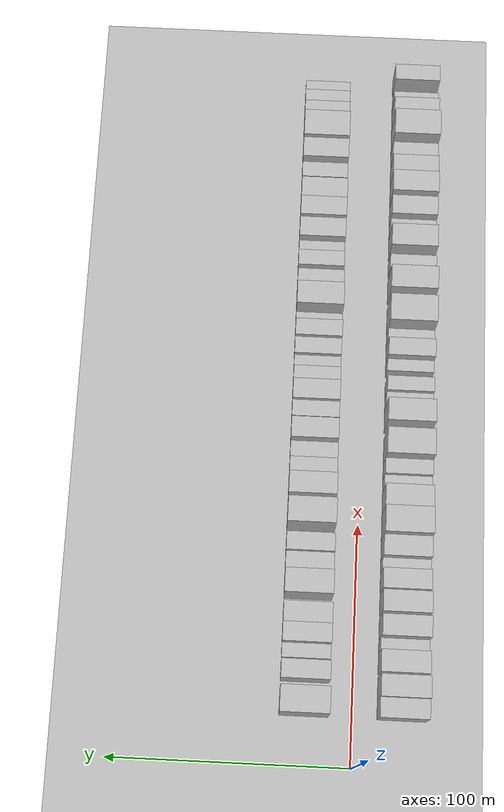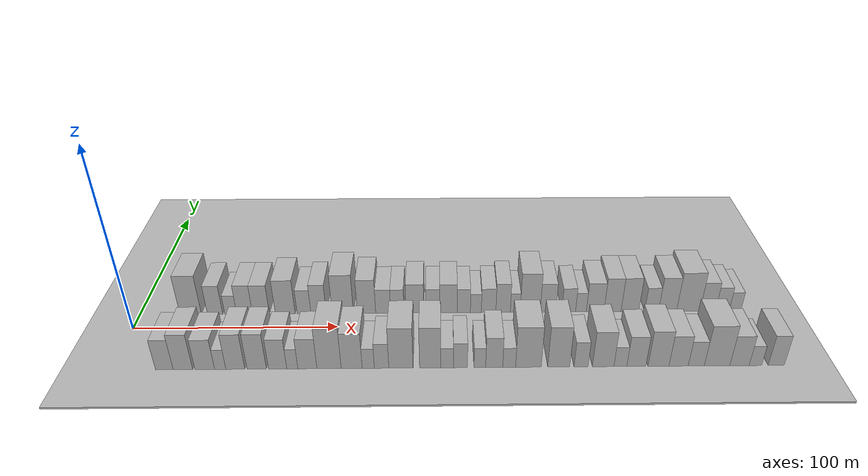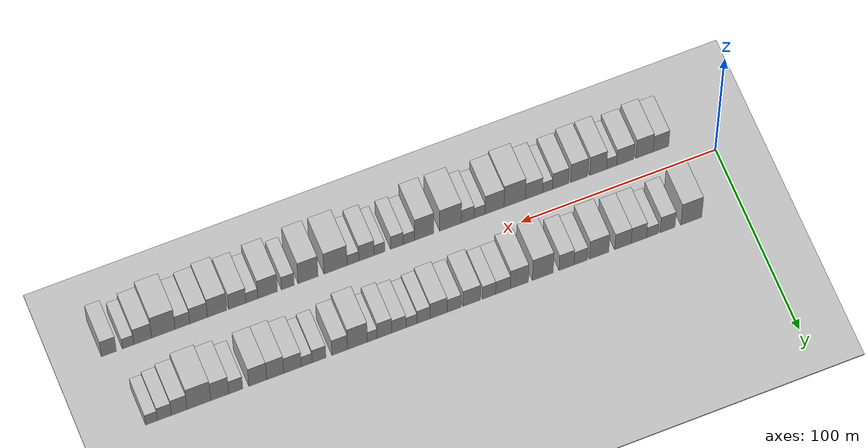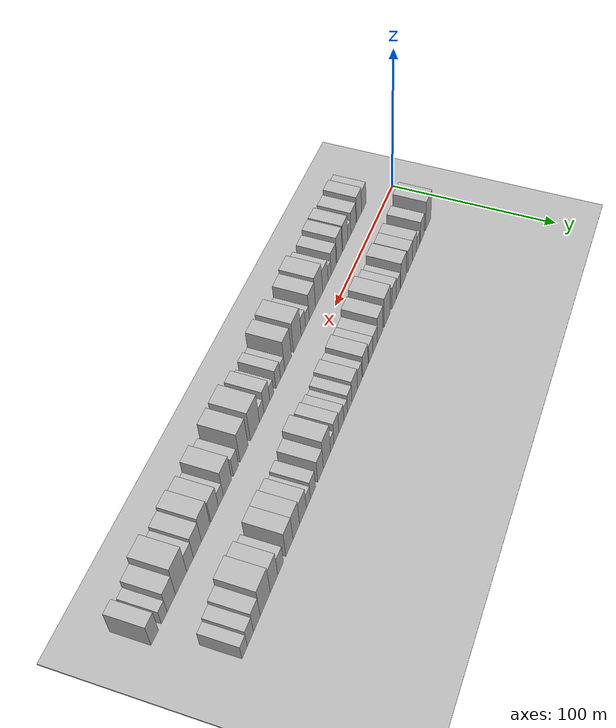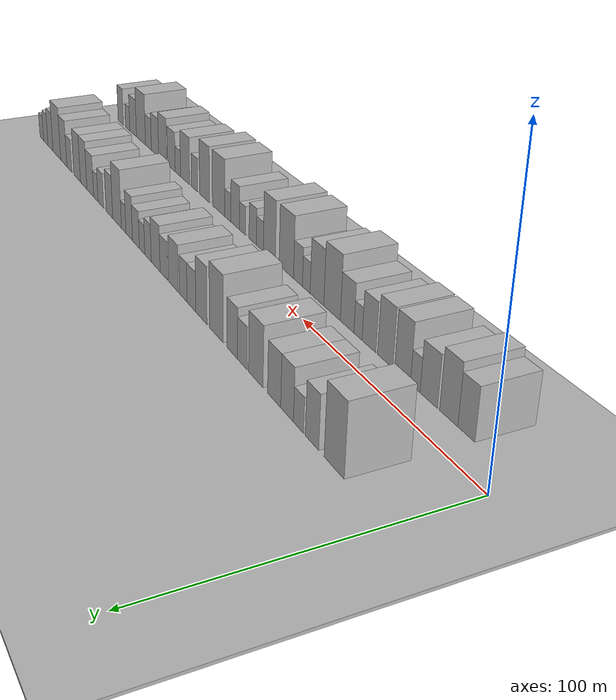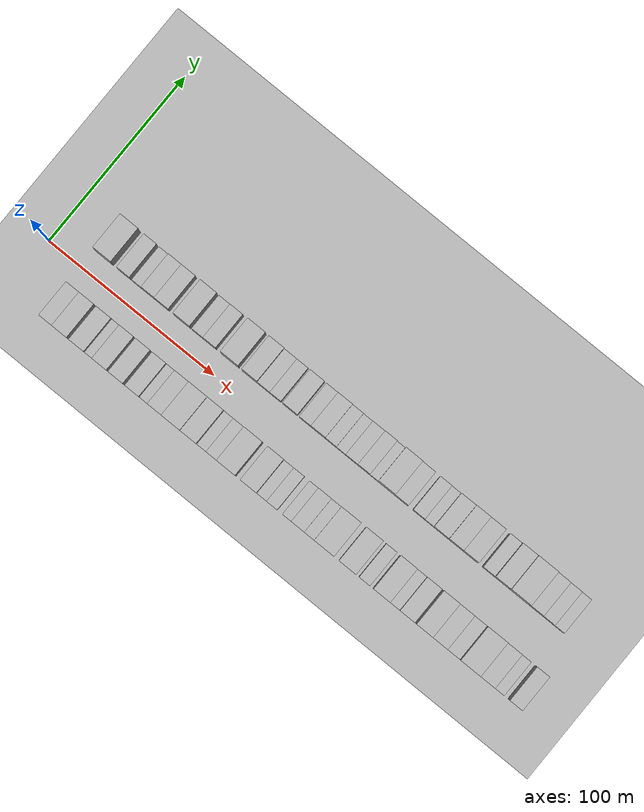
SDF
<?xml version="1.0" encoding="utf-8"?>

<sdf version="1.6">

   <world name="default">

      <gui fullscreen="0">

         <camera name="user_camera">

            <pose>-15 0 4.57585 0 0 0</pose>

            <view_controller>orbit</view_controller>

         </camera>

      </gui>

      <scene>

         <sky>

           <clouds>

             <speed>12</speed>

           </clouds>

         </sky>

         <ambient>0.4 0.4 0.4 1</ambient>

         <background>0.7 0.7 0.7 1</background>

         <shadows>1</shadows>

      </scene>

      <gravity>0 0 -9.8066</gravity>

      <magnetic_field>6e-06 2.3e-05 -4.2e-05</magnetic_field>

      <physics default="0" name="default_physics" type="ode">

         <ode>

            <solver>

               <type>quick</type>

               <iters>10</iters>

               <sor>1.0</sor>

               <use_dynamic_moi_rescaling>0</use_dynamic_moi_rescaling>

            </solver>

            <constraints>

               <cfm>0</cfm>

               <erp>0.2</erp>

               <contact_max_correcting_vel>100</contact_max_correcting_vel>

               <contact_surface_layer>0.001</contact_surface_layer>

            </constraints>

         </ode>

         <max_step_size>0.004</max_step_size>

         <real_time_factor>1</real_time_factor>

         <real_time_update_rate>250</real_time_update_rate>

      </physics>

      <light name="sun" type="directional">

         <cast_shadows>1</cast_shadows>

         <pose>0 0 10 0 0 0</pose>

         <diffuse>0.8 0.8 0.8 1</diffuse>

         <specular>0.2 0.2 0.2 1</specular>

         <attenuation>

            <range>1000</range>

            <constant>0.9</constant>

            <linear>0.01</linear>

            <quadratic>0.001</quadratic>

         </attenuation>

         <direction>-0.5 0.1 -0.9</direction>

      </light>

      <include>

         <name>ground_plane_1</name>

         <uri>model://HANNAS_ground_plane</uri>

         <pose>0 0 0  0 0 0</pose>

      </include>

      <include>

         <name>ground_plane_2</name>

         <uri>model://HANNAS_ground_plane</uri>

         <pose>100 0 0  0 0 0</pose>

      </include>

      <model name="building_1">

         <static>1</static>

         <pose frame="">25.3760 20.0000 0 0.000000 0.000000 1.570796</pose>

         <link name="link">

            <pose frame="">0 0 12.00 0 0 0</pose>

            <collision name="collision">

               <geometry>

                  <box>

                     <size>20.0000 10.7519 24.0000</size>

                  </box>

               </geometry>

               <max_contacts>10</max_contacts>

               <surface>

                  <contact>

                     <ode/>

                  </contact>

                  <bounce/>

                  <friction>

                     <torsional>

                        <ode/>

                     </torsional>

                     <ode/>

                  </friction>

               </surface>

            </collision>

            <visual name="visual">

               <cast_shadows>0</cast_shadows>

               <geometry>

                  <box>

                     <size>20.0000 10.7519 24.0000</size>

                  </box>

               </geometry>

               <material>

                  <script>

                     <uri>model://HANNAS_wall/materials/scripts</uri>

                     <uri>model://HANNAS_wall/materials/textures</uri>

                     <name>vrc/HANNAS_wall</name>

                  </script>

               </material>

            </visual>

            <self_collide>0</self_collide>

            <enable_wind>0</enable_wind>

            <kinematic>0</kinematic>

         </link>

      </model>

      <model name="building_2">

         <static>1</static>

         <pose frame="">37.5861 20.0000 0 0.000000 0.000000 1.570796</pose>

         <link name="link">

            <pose frame="">0 0 9.00 0 0 0</pose>

            <collision name="collision">

               <geometry>

                  <box>

                     <size>20.0000 7.6683 18.0000</size>

                  </box>

               </geometry>

               <max_contacts>10</max_contacts>

               <surface>

                  <contact>

                     <ode/>

                  </contact>

                  <bounce/>

                  <friction>

                     <torsional>

                        <ode/>

                     </torsional>

                     <ode/>

                  </friction>

               </surface>

            </collision>

            <visual name="visual">

               <cast_shadows>0</cast_shadows>

               <geometry>

                  <box>

                     <size>20.0000 7.6683 18.0000</size>

                  </box>

               </geometry>

               <material>

                  <script>

                     <uri>model://HANNAS_wall/materials/scripts</uri>

                     <uri>model://HANNAS_wall/materials/textures</uri>

                     <name>vrc/HANNAS_wall</name>

                  </script>

               </material>

            </visual>

            <self_collide>0</self_collide>

            <enable_wind>0</enable_wind>

            <kinematic>0</kinematic>

         </link>

      </model>

      <model name="building_3">

         <static>1</static>

         <pose frame="">45.4054 20.0000 0 0.000000 0.000000 1.570796</pose>

         <link name="link">

            <pose frame="">0 0 6.00 0 0 0</pose>

            <collision name="collision">

               <geometry>

                  <box>

                     <size>20.0000 5.9705 12.0000</size>

                  </box>

               </geometry>

               <max_contacts>10</max_contacts>

               <surface>

                  <contact>

                     <ode/>

                  </contact>

                  <bounce/>

                  <friction>

                     <torsional>

                        <ode/>

                     </torsional>

                     <ode/>

                  </friction>

               </surface>

            </collision>

            <visual name="visual">

               <cast_shadows>0</cast_shadows>

               <geometry>

                  <box>

                     <size>20.0000 5.9705 12.0000</size>

                  </box>

               </geometry>

               <material>

                  <script>

                     <uri>model://HANNAS_wall/materials/scripts</uri>

                     <uri>model://HANNAS_wall/materials/textures</uri>

                     <name>vrc/HANNAS_wall</name>

                  </script>

               </material>

            </visual>

            <self_collide>0</self_collide>

            <enable_wind>0</enable_wind>

            <kinematic>0</kinematic>

         </link>

      </model>

      <model name="building_4">

         <static>1</static>

         <pose frame="">52.3289 20.0000 0 0.000000 0.000000 1.570796</pose>

         <link name="link">

            <pose frame="">0 0 9.00 0 0 0</pose>

            <collision name="collision">

               <geometry>

                  <box>

                     <size>20.0000 7.8765 18.0000</size>

                  </box>

               </geometry>

               <max_contacts>10</max_contacts>

               <surface>

                  <contact>

                     <ode/>

                  </contact>

                  <bounce/>

                  <friction>

                     <torsional>

                        <ode/>

                     </torsional>

                     <ode/>

                  </friction>

               </surface>

            </collision>

            <visual name="visual">

               <cast_shadows>0</cast_shadows>

               <geometry>

                  <box>

                     <size>20.0000 7.8765 18.0000</size>

                  </box>

               </geometry>

               <material>

                  <script>

                     <uri>model://HANNAS_wall/materials/scripts</uri>

                     <uri>model://HANNAS_wall/materials/textures</uri>

                     <name>vrc/HANNAS_wall</name>

                  </script>

               </material>

            </visual>

            <self_collide>0</self_collide>

            <enable_wind>0</enable_wind>

            <kinematic>0</kinematic>

         </link>

      </model>

      <model name="building_5">

         <static>1</static>

         <pose frame="">60.4882 20.0000 0 0.000000 0.000000 1.570796</pose>

         <link name="link">

            <pose frame="">0 0 9.00 0 0 0</pose>

            <collision name="collision">

               <geometry>

                  <box>

                     <size>20.0000 8.4420 18.0000</size>

                  </box>

               </geometry>

               <max_contacts>10</max_contacts>

               <surface>

                  <contact>

                     <ode/>

                  </contact>

                  <bounce/>

                  <friction>

                     <torsional>

                        <ode/>

                     </torsional>

                     <ode/>

                  </friction>

               </surface>

            </collision>

            <visual name="visual">

               <cast_shadows>0</cast_shadows>

               <geometry>

                  <box>

                     <size>20.0000 8.4420 18.0000</size>

                  </box>

               </geometry>

               <material>

                  <script>

                     <uri>model://HANNAS_wall/materials/scripts</uri>

                     <uri>model://HANNAS_wall/materials/textures</uri>

                     <name>vrc/HANNAS_wall</name>

                  </script>

               </material>

            </visual>

            <self_collide>0</self_collide>

            <enable_wind>0</enable_wind>

            <kinematic>0</kinematic>

         </link>

      </model>

      <model name="building_6">

         <static>1</static>

         <pose frame="">72.6612 20.0000 0 0.000000 0.000000 1.570796</pose>

         <link name="link">

            <pose frame="">0 0 10.50 0 0 0</pose>

            <collision name="collision">

               <geometry>

                  <box>

                     <size>20.0000 9.9039 21.0000</size>

                  </box>

               </geometry>

               <max_contacts>10</max_contacts>

               <surface>

                  <contact>

                     <ode/>

                  </contact>

                  <bounce/>

                  <friction>

                     <torsional>

                        <ode/>

                     </torsional>

                     <ode/>

                  </friction>

               </surface>

            </collision>

            <visual name="visual">

               <cast_shadows>0</cast_shadows>

               <geometry>

                  <box>

                     <size>20.0000 9.9039 21.0000</size>

                  </box>

               </geometry>

               <material>

                  <script>

                     <uri>model://HANNAS_wall/materials/scripts</uri>

                     <uri>model://HANNAS_wall/materials/textures</uri>

                     <name>vrc/HANNAS_wall</name>

                  </script>

               </material>

            </visual>

            <self_collide>0</self_collide>

            <enable_wind>0</enable_wind>

            <kinematic>0</kinematic>

         </link>

      </model>

      <model name="building_7">

         <static>1</static>

         <pose frame="">82.0439 20.0000 0 0.000000 0.000000 1.570796</pose>

         <link name="link">

            <pose frame="">0 0 7.50 0 0 0</pose>

            <collision name="collision">

               <geometry>

                  <box>

                     <size>20.0000 6.8616 15.0000</size>

                  </box>

               </geometry>

               <max_contacts>10</max_contacts>

               <surface>

                  <contact>

                     <ode/>

                  </contact>

                  <bounce/>

                  <friction>

                     <torsional>

                        <ode/>

                     </torsional>

                     <ode/>

                  </friction>

               </surface>

            </collision>

            <visual name="visual">

               <cast_shadows>0</cast_shadows>

               <geometry>

                  <box>

                     <size>20.0000 6.8616 15.0000</size>

                  </box>

               </geometry>

               <material>

                  <script>

                     <uri>model://HANNAS_wall/materials/scripts</uri>

                     <uri>model://HANNAS_wall/materials/textures</uri>

                     <name>vrc/HANNAS_wall</name>

                  </script>

               </material>

            </visual>

            <self_collide>0</self_collide>

            <enable_wind>0</enable_wind>

            <kinematic>0</kinematic>

         </link>

      </model>

      <model name="building_8">

         <static>1</static>

         <pose frame="">89.3051 20.0000 0 0.000000 0.000000 1.570796</pose>

         <link name="link">

            <pose frame="">0 0 9.00 0 0 0</pose>

            <collision name="collision">

               <geometry>

                  <box>

                     <size>20.0000 7.6608 18.0000</size>

                  </box>

               </geometry>

               <max_contacts>10</max_contacts>

               <surface>

                  <contact>

                     <ode/>

                  </contact>

                  <bounce/>

                  <friction>

                     <torsional>

                        <ode/>

                     </torsional>

                     <ode/>

                  </friction>

               </surface>

            </collision>

            <visual name="visual">

               <cast_shadows>0</cast_shadows>

               <geometry>

                  <box>

                     <size>20.0000 7.6608 18.0000</size>

                  </box>

               </geometry>

               <material>

                  <script>

                     <uri>model://HANNAS_wall/materials/scripts</uri>

                     <uri>model://HANNAS_wall/materials/textures</uri>

                     <name>vrc/HANNAS_wall</name>

                  </script>

               </material>

            </visual>

            <self_collide>0</self_collide>

            <enable_wind>0</enable_wind>

            <kinematic>0</kinematic>

         </link>

      </model>

      <model name="building_9">

         <static>1</static>

         <pose frame="">101.4516 20.0000 0 0.000000 0.000000 1.570796</pose>

         <link name="link">

            <pose frame="">0 0 12.00 0 0 0</pose>

            <collision name="collision">

               <geometry>

                  <box>

                     <size>20.0000 10.6323 24.0000</size>

                  </box>

               </geometry>

               <max_contacts>10</max_contacts>

               <surface>

                  <contact>

                     <ode/>

                  </contact>

                  <bounce/>

                  <friction>

                     <torsional>

                        <ode/>

                     </torsional>

                     <ode/>

                  </friction>

               </surface>

            </collision>

            <visual name="visual">

               <cast_shadows>0</cast_shadows>

               <geometry>

                  <box>

                     <size>20.0000 10.6323 24.0000</size>

                  </box>

               </geometry>

               <material>

                  <script>

                     <uri>model://HANNAS_wall/materials/scripts</uri>

                     <uri>model://HANNAS_wall/materials/textures</uri>

                     <name>vrc/HANNAS_wall</name>

                  </script>

               </material>

            </visual>

            <self_collide>0</self_collide>

            <enable_wind>0</enable_wind>

            <kinematic>0</kinematic>

         </link>

      </model>

      <model name="building_10">

         <static>1</static>

         <pose frame="">113.3578 20.0000 0 0.000000 0.000000 1.570796</pose>

         <link name="link">

            <pose frame="">0 0 10.50 0 0 0</pose>

            <collision name="collision">

               <geometry>

                  <box>

                     <size>20.0000 9.1799 21.0000</size>

                  </box>

               </geometry>

               <max_contacts>10</max_contacts>

               <surface>

                  <contact>

                     <ode/>

                  </contact>

                  <bounce/>

                  <friction>

                     <torsional>

                        <ode/>

                     </torsional>

                     <ode/>

                  </friction>

               </surface>

            </collision>

            <visual name="visual">

               <cast_shadows>0</cast_shadows>

               <geometry>

                  <box>

                     <size>20.0000 9.1799 21.0000</size>

                  </box>

               </geometry>

               <material>

                  <script>

                     <uri>model://HANNAS_wall/materials/scripts</uri>

                     <uri>model://HANNAS_wall/materials/textures</uri>

                     <name>vrc/HANNAS_wall</name>

                  </script>

               </material>

            </visual>

            <self_collide>0</self_collide>

            <enable_wind>0</enable_wind>

            <kinematic>0</kinematic>

         </link>

      </model>

      <model name="building_11">

         <static>1</static>

         <pose frame="">121.6955 20.0000 0 0.000000 0.000000 1.570796</pose>

         <link name="link">

            <pose frame="">0 0 7.50 0 0 0</pose>

            <collision name="collision">

               <geometry>

                  <box>

                     <size>20.0000 7.4956 15.0000</size>

                  </box>

               </geometry>

               <max_contacts>10</max_contacts>

               <surface>

                  <contact>

                     <ode/>

                  </contact>

                  <bounce/>

                  <friction>

                     <torsional>

                        <ode/>

                     </torsional>

                     <ode/>

                  </friction>

               </surface>

            </collision>

            <visual name="visual">

               <cast_shadows>0</cast_shadows>

               <geometry>

                  <box>

                     <size>20.0000 7.4956 15.0000</size>

                  </box>

               </geometry>

               <material>

                  <script>

                     <uri>model://HANNAS_wall/materials/scripts</uri>

                     <uri>model://HANNAS_wall/materials/textures</uri>

                     <name>vrc/HANNAS_wall</name>

                  </script>

               </material>

            </visual>

            <self_collide>0</self_collide>

            <enable_wind>0</enable_wind>

            <kinematic>0</kinematic>

         </link>

      </model>

      <model name="building_12">

         <static>1</static>

         <pose frame="">128.8012 20.0000 0 0.000000 0.000000 1.570796</pose>

         <link name="link">

            <pose frame="">0 0 7.50 0 0 0</pose>

            <collision name="collision">

               <geometry>

                  <box>

                     <size>20.0000 6.7157 15.0000</size>

                  </box>

               </geometry>

               <max_contacts>10</max_contacts>

               <surface>

                  <contact>

                     <ode/>

                  </contact>

                  <bounce/>

                  <friction>

                     <torsional>

                        <ode/>

                     </torsional>

                     <ode/>

                  </friction>

               </surface>

            </collision>

            <visual name="visual">

               <cast_shadows>0</cast_shadows>

               <geometry>

                  <box>

                     <size>20.0000 6.7157 15.0000</size>

                  </box>

               </geometry>

               <material>

                  <script>

                     <uri>model://HANNAS_wall/materials/scripts</uri>

                     <uri>model://HANNAS_wall/materials/textures</uri>

                     <name>vrc/HANNAS_wall</name>

                  </script>

               </material>

            </visual>

            <self_collide>0</self_collide>

            <enable_wind>0</enable_wind>

            <kinematic>0</kinematic>

         </link>

      </model>

      <model name="building_13">

         <static>1</static>

         <pose frame="">137.6105 20.0000 0 0.000000 0.000000 1.570796</pose>

         <link name="link">

            <pose frame="">0 0 9.00 0 0 0</pose>

            <collision name="collision">

               <geometry>

                  <box>

                     <size>20.0000 8.9029 18.0000</size>

                  </box>

               </geometry>

               <max_contacts>10</max_contacts>

               <surface>

                  <contact>

                     <ode/>

                  </contact>

                  <bounce/>

                  <friction>

                     <torsional>

                        <ode/>

                     </torsional>

                     <ode/>

                  </friction>

               </surface>

            </collision>

            <visual name="visual">

               <cast_shadows>0</cast_shadows>

               <geometry>

                  <box>

                     <size>20.0000 8.9029 18.0000</size>

                  </box>

               </geometry>

               <material>

                  <script>

                     <uri>model://HANNAS_wall/materials/scripts</uri>

                     <uri>model://HANNAS_wall/materials/textures</uri>

                     <name>vrc/HANNAS_wall</name>

                  </script>

               </material>

            </visual>

            <self_collide>0</self_collide>

            <enable_wind>0</enable_wind>

            <kinematic>0</kinematic>

         </link>

      </model>

      <model name="building_14">

         <static>1</static>

         <pose frame="">146.5816 20.0000 0 0.000000 0.000000 1.570796</pose>

         <link name="link">

            <pose frame="">0 0 7.50 0 0 0</pose>

            <collision name="collision">

               <geometry>

                  <box>

                     <size>20.0000 7.0394 15.0000</size>

                  </box>

               </geometry>

               <max_contacts>10</max_contacts>

               <surface>

                  <contact>

                     <ode/>

                  </contact>

                  <bounce/>

                  <friction>

                     <torsional>

                        <ode/>

                     </torsional>

                     <ode/>

                  </friction>

               </surface>

            </collision>

            <visual name="visual">

               <cast_shadows>0</cast_shadows>

               <geometry>

                  <box>

                     <size>20.0000 7.0394 15.0000</size>

                  </box>

               </geometry>

               <material>

                  <script>

                     <uri>model://HANNAS_wall/materials/scripts</uri>

                     <uri>model://HANNAS_wall/materials/textures</uri>

                     <name>vrc/HANNAS_wall</name>

                  </script>

               </material>

            </visual>

            <self_collide>0</self_collide>

            <enable_wind>0</enable_wind>

            <kinematic>0</kinematic>

         </link>

      </model>

      <model name="building_15">

         <static>1</static>

         <pose frame="">154.4547 20.0000 0 0.000000 0.000000 1.570796</pose>

         <link name="link">

            <pose frame="">0 0 9.00 0 0 0</pose>

            <collision name="collision">

               <geometry>

                  <box>

                     <size>20.0000 8.7069 18.0000</size>

                  </box>

               </geometry>

               <max_contacts>10</max_contacts>

               <surface>

                  <contact>

                     <ode/>

                  </contact>

                  <bounce/>

                  <friction>

                     <torsional>

                        <ode/>

                     </torsional>

                     <ode/>

                  </friction>

               </surface>

            </collision>

            <visual name="visual">

               <cast_shadows>0</cast_shadows>

               <geometry>

                  <box>

                     <size>20.0000 8.7069 18.0000</size>

                  </box>

               </geometry>

               <material>

                  <script>

                     <uri>model://HANNAS_wall/materials/scripts</uri>

                     <uri>model://HANNAS_wall/materials/textures</uri>

                     <name>vrc/HANNAS_wall</name>

                  </script>

               </material>

            </visual>

            <self_collide>0</self_collide>

            <enable_wind>0</enable_wind>

            <kinematic>0</kinematic>

         </link>

      </model>

      <model name="building_16">

         <static>1</static>

         <pose frame="">162.1069 20.0000 0 0.000000 0.000000 1.570796</pose>

         <link name="link">

            <pose frame="">0 0 7.50 0 0 0</pose>

            <collision name="collision">

               <geometry>

                  <box>

                     <size>20.0000 6.5975 15.0000</size>

                  </box>

               </geometry>

               <max_contacts>10</max_contacts>

               <surface>

                  <contact>

                     <ode/>

                  </contact>

                  <bounce/>

                  <friction>

                     <torsional>

                        <ode/>

                     </torsional>

                     <ode/>

                  </friction>

               </surface>

            </collision>

            <visual name="visual">

               <cast_shadows>0</cast_shadows>

               <geometry>

                  <box>

                     <size>20.0000 6.5975 15.0000</size>

                  </box>

               </geometry>

               <material>

                  <script>

                     <uri>model://HANNAS_wall/materials/scripts</uri>

                     <uri>model://HANNAS_wall/materials/textures</uri>

                     <name>vrc/HANNAS_wall</name>

                  </script>

               </material>

            </visual>

            <self_collide>0</self_collide>

            <enable_wind>0</enable_wind>

            <kinematic>0</kinematic>

         </link>

      </model>

      <model name="building_17">

         <static>1</static>

         <pose frame="">168.1742 20.0000 0 0.000000 0.000000 1.570796</pose>

         <link name="link">

            <pose frame="">0 0 6.00 0 0 0</pose>

            <collision name="collision">

               <geometry>

                  <box>

                     <size>20.0000 5.5370 12.0000</size>

                  </box>

               </geometry>

               <max_contacts>10</max_contacts>

               <surface>

                  <contact>

                     <ode/>

                  </contact>

                  <bounce/>

                  <friction>

                     <torsional>

                        <ode/>

                     </torsional>

                     <ode/>

                  </friction>

               </surface>

            </collision>

            <visual name="visual">

               <cast_shadows>0</cast_shadows>

               <geometry>

                  <box>

                     <size>20.0000 5.5370 12.0000</size>

                  </box>

               </geometry>

               <material>

                  <script>

                     <uri>model://HANNAS_wall/materials/scripts</uri>

                     <uri>model://HANNAS_wall/materials/textures</uri>

                     <name>vrc/HANNAS_wall</name>

                  </script>

               </material>

            </visual>

            <self_collide>0</self_collide>

            <enable_wind>0</enable_wind>

            <kinematic>0</kinematic>

         </link>

      </model>

      <model name="building_18">

         <static>1</static>

         <pose frame="">174.5783 20.0000 0 0.000000 0.000000 1.570796</pose>

         <link name="link">

            <pose frame="">0 0 7.50 0 0 0</pose>

            <collision name="collision">

               <geometry>

                  <box>

                     <size>20.0000 7.2712 15.0000</size>

                  </box>

               </geometry>

               <max_contacts>10</max_contacts>

               <surface>

                  <contact>

                     <ode/>

                  </contact>

                  <bounce/>

                  <friction>

                     <torsional>

                        <ode/>

                     </torsional>

                     <ode/>

                  </friction>

               </surface>

            </collision>

            <visual name="visual">

               <cast_shadows>0</cast_shadows>

               <geometry>

                  <box>

                     <size>20.0000 7.2712 15.0000</size>

                  </box>

               </geometry>

               <material>

                  <script>

                     <uri>model://HANNAS_wall/materials/scripts</uri>

                     <uri>model://HANNAS_wall/materials/textures</uri>

                     <name>vrc/HANNAS_wall</name>

                  </script>

               </material>

            </visual>

            <self_collide>0</self_collide>

            <enable_wind>0</enable_wind>

            <kinematic>0</kinematic>

         </link>

      </model>

      <model name="building_19">

         <static>1</static>

         <pose frame="">181.8571 20.0000 0 0.000000 0.000000 1.570796</pose>

         <link name="link">

            <pose frame="">0 0 9.00 0 0 0</pose>

            <collision name="collision">

               <geometry>

                  <box>

                     <size>20.0000 7.2865 18.0000</size>

                  </box>

               </geometry>

               <max_contacts>10</max_contacts>

               <surface>

                  <contact>

                     <ode/>

                  </contact>

                  <bounce/>

                  <friction>

                     <torsional>

                        <ode/>

                     </torsional>

                     <ode/>

                  </friction>

               </surface>

            </collision>

            <visual name="visual">

               <cast_shadows>0</cast_shadows>

               <geometry>

                  <box>

                     <size>20.0000 7.2865 18.0000</size>

                  </box>

               </geometry>

               <material>

                  <script>

                     <uri>model://HANNAS_wall/materials/scripts</uri>

                     <uri>model://HANNAS_wall/materials/textures</uri>

                     <name>vrc/HANNAS_wall</name>

                  </script>

               </material>

            </visual>

            <self_collide>0</self_collide>

            <enable_wind>0</enable_wind>

            <kinematic>0</kinematic>

         </link>

      </model>

      <model name="building_20">

         <static>1</static>

         <pose frame="">187.9732 20.0000 0 0.000000 0.000000 1.570796</pose>

         <link name="link">

            <pose frame="">0 0 6.00 0 0 0</pose>

            <collision name="collision">

               <geometry>

                  <box>

                     <size>20.0000 4.9458 12.0000</size>

                  </box>

               </geometry>

               <max_contacts>10</max_contacts>

               <surface>

                  <contact>

                     <ode/>

                  </contact>

                  <bounce/>

                  <friction>

                     <torsional>

                        <ode/>

                     </torsional>

                     <ode/>

                  </friction>

               </surface>

            </collision>

            <visual name="visual">

               <cast_shadows>0</cast_shadows>

               <geometry>

                  <box>

                     <size>20.0000 4.9458 12.0000</size>

                  </box>

               </geometry>

               <material>

                  <script>

                     <uri>model://HANNAS_wall/materials/scripts</uri>

                     <uri>model://HANNAS_wall/materials/textures</uri>

                     <name>vrc/HANNAS_wall</name>

                  </script>

               </material>

            </visual>

            <self_collide>0</self_collide>

            <enable_wind>0</enable_wind>

            <kinematic>0</kinematic>

         </link>

      </model>

      <model name="building_21">

         <static>1</static>

         <pose frame="">195.4713 20.0000 0 0.000000 0.000000 1.570796</pose>

         <link name="link">

            <pose frame="">0 0 12.00 0 0 0</pose>

            <collision name="collision">

               <geometry>

                  <box>

                     <size>20.0000 10.0504 24.0000</size>

                  </box>

               </geometry>

               <max_contacts>10</max_contacts>

               <surface>

                  <contact>

                     <ode/>

                  </contact>

                  <bounce/>

                  <friction>

                     <torsional>

                        <ode/>

                     </torsional>

                     <ode/>

                  </friction>

               </surface>

            </collision>

            <visual name="visual">

               <cast_shadows>0</cast_shadows>

               <geometry>

                  <box>

                     <size>20.0000 10.0504 24.0000</size>

                  </box>

               </geometry>

               <material>

                  <script>

                     <uri>model://HANNAS_wall/materials/scripts</uri>

                     <uri>model://HANNAS_wall/materials/textures</uri>

                     <name>vrc/HANNAS_wall</name>

                  </script>

               </material>

            </visual>

            <self_collide>0</self_collide>

            <enable_wind>0</enable_wind>

            <kinematic>0</kinematic>

         </link>

      </model>

      <model name="building_22">

         <static>1</static>

         <pose frame="">204.4331 20.0000 0 0.000000 0.000000 1.570796</pose>

         <link name="link">

            <pose frame="">0 0 9.00 0 0 0</pose>

            <collision name="collision">

               <geometry>

                  <box>

                     <size>20.0000 7.8732 18.0000</size>

                  </box>

               </geometry>

               <max_contacts>10</max_contacts>

               <surface>

                  <contact>

                     <ode/>

                  </contact>

                  <bounce/>

                  <friction>

                     <torsional>

                        <ode/>

                     </torsional>

                     <ode/>

                  </friction>

               </surface>

            </collision>

            <visual name="visual">

               <cast_shadows>0</cast_shadows>

               <geometry>

                  <box>

                     <size>20.0000 7.8732 18.0000</size>

                  </box>

               </geometry>

               <material>

                  <script>

                     <uri>model://HANNAS_wall/materials/scripts</uri>

                     <uri>model://HANNAS_wall/materials/textures</uri>

                     <name>vrc/HANNAS_wall</name>

                  </script>

               </material>

            </visual>

            <self_collide>0</self_collide>

            <enable_wind>0</enable_wind>

            <kinematic>0</kinematic>

         </link>

      </model>

      <model name="building_23">

         <static>1</static>

         <pose frame="">214.8274 20.0000 0 0.000000 0.000000 1.570796</pose>

         <link name="link">

            <pose frame="">0 0 7.50 0 0 0</pose>

            <collision name="collision">

               <geometry>

                  <box>

                     <size>20.0000 6.9155 15.0000</size>

                  </box>

               </geometry>

               <max_contacts>10</max_contacts>

               <surface>

                  <contact>

                     <ode/>

                  </contact>

                  <bounce/>

                  <friction>

                     <torsional>

                        <ode/>

                     </torsional>

                     <ode/>

                  </friction>

               </surface>

            </collision>

            <visual name="visual">

               <cast_shadows>0</cast_shadows>

               <geometry>

                  <box>

                     <size>20.0000 6.9155 15.0000</size>

                  </box>

               </geometry>

               <material>

                  <script>

                     <uri>model://HANNAS_wall/materials/scripts</uri>

                     <uri>model://HANNAS_wall/materials/textures</uri>

                     <name>vrc/HANNAS_wall</name>

                  </script>

               </material>

            </visual>

            <self_collide>0</self_collide>

            <enable_wind>0</enable_wind>

            <kinematic>0</kinematic>

         </link>

      </model>

      <model name="building_24">

         <static>1</static>

         <pose frame="">221.0099 20.0000 0 0.000000 0.000000 1.570796</pose>

         <link name="link">

            <pose frame="">0 0 6.00 0 0 0</pose>

            <collision name="collision">

               <geometry>

                  <box>

                     <size>20.0000 5.4495 12.0000</size>

                  </box>

               </geometry>

               <max_contacts>10</max_contacts>

               <surface>

                  <contact>

                     <ode/>

                  </contact>

                  <bounce/>

                  <friction>

                     <torsional>

                        <ode/>

                     </torsional>

                     <ode/>

                  </friction>

               </surface>

            </collision>

            <visual name="visual">

               <cast_shadows>0</cast_shadows>

               <geometry>

                  <box>

                     <size>20.0000 5.4495 12.0000</size>

                  </box>

               </geometry>

               <material>

                  <script>

                     <uri>model://HANNAS_wall/materials/scripts</uri>

                     <uri>model://HANNAS_wall/materials/textures</uri>

                     <name>vrc/HANNAS_wall</name>

                  </script>

               </material>

            </visual>

            <self_collide>0</self_collide>

            <enable_wind>0</enable_wind>

            <kinematic>0</kinematic>

         </link>

      </model>

      <model name="building_25">

         <static>1</static>

         <pose frame="">228.1481 20.0000 0 0.000000 0.000000 1.570796</pose>

         <link name="link">

            <pose frame="">0 0 9.00 0 0 0</pose>

            <collision name="collision">

               <geometry>

                  <box>

                     <size>20.0000 8.8268 18.0000</size>

                  </box>

               </geometry>

               <max_contacts>10</max_contacts>

               <surface>

                  <contact>

                     <ode/>

                  </contact>

                  <bounce/>

                  <friction>

                     <torsional>

                        <ode/>

                     </torsional>

                     <ode/>

                  </friction>

               </surface>

            </collision>

            <visual name="visual">

               <cast_shadows>0</cast_shadows>

               <geometry>

                  <box>

                     <size>20.0000 8.8268 18.0000</size>

                  </box>

               </geometry>

               <material>

                  <script>

                     <uri>model://HANNAS_wall/materials/scripts</uri>

                     <uri>model://HANNAS_wall/materials/textures</uri>

                     <name>vrc/HANNAS_wall</name>

                  </script>

               </material>

            </visual>

            <self_collide>0</self_collide>

            <enable_wind>0</enable_wind>

            <kinematic>0</kinematic>

         </link>

      </model>

      <model name="building_26">

         <static>1</static>

         <pose frame="">236.8803 20.0000 0 0.000000 0.000000 1.570796</pose>

         <link name="link">

            <pose frame="">0 0 10.50 0 0 0</pose>

            <collision name="collision">

               <geometry>

                  <box>

                     <size>20.0000 8.6376 21.0000</size>

                  </box>

               </geometry>

               <max_contacts>10</max_contacts>

               <surface>

                  <contact>

                     <ode/>

                  </contact>

                  <bounce/>

                  <friction>

                     <torsional>

                        <ode/>

                     </torsional>

                     <ode/>

                  </friction>

               </surface>

            </collision>

            <visual name="visual">

               <cast_shadows>0</cast_shadows>

               <geometry>

                  <box>

                     <size>20.0000 8.6376 21.0000</size>

                  </box>

               </geometry>

               <material>

                  <script>

                     <uri>model://HANNAS_wall/materials/scripts</uri>

                     <uri>model://HANNAS_wall/materials/textures</uri>

                     <name>vrc/HANNAS_wall</name>

                  </script>

               </material>

            </visual>

            <self_collide>0</self_collide>

            <enable_wind>0</enable_wind>

            <kinematic>0</kinematic>

         </link>

      </model>

      <model name="building_27">

         <static>1</static>

         <pose frame="">245.6707 20.0000 0 0.000000 0.000000 1.570796</pose>

         <link name="link">

            <pose frame="">0 0 10.50 0 0 0</pose>

            <collision name="collision">

               <geometry>

                  <box>

                     <size>20.0000 8.9432 21.0000</size>

                  </box>

               </geometry>

               <max_contacts>10</max_contacts>

               <surface>

                  <contact>

                     <ode/>

                  </contact>

                  <bounce/>

                  <friction>

                     <torsional>

                        <ode/>

                     </torsional>

                     <ode/>

                  </friction>

               </surface>

            </collision>

            <visual name="visual">

               <cast_shadows>0</cast_shadows>

               <geometry>

                  <box>

                     <size>20.0000 8.9432 21.0000</size>

                  </box>

               </geometry>

               <material>

                  <script>

                     <uri>model://HANNAS_wall/materials/scripts</uri>

                     <uri>model://HANNAS_wall/materials/textures</uri>

                     <name>vrc/HANNAS_wall</name>

                  </script>

               </material>

            </visual>

            <self_collide>0</self_collide>

            <enable_wind>0</enable_wind>

            <kinematic>0</kinematic>

         </link>

      </model>

      <model name="building_28">

         <static>1</static>

         <pose frame="">256.6422 20.0000 0 0.000000 0.000000 1.570796</pose>

         <link name="link">

            <pose frame="">0 0 7.50 0 0 0</pose>

            <collision name="collision">

               <geometry>

                  <box>

                     <size>20.0000 6.9999 15.0000</size>

                  </box>

               </geometry>

               <max_contacts>10</max_contacts>

               <surface>

                  <contact>

                     <ode/>

                  </contact>

                  <bounce/>

                  <friction>

                     <torsional>

                        <ode/>

                     </torsional>

                     <ode/>

                  </friction>

               </surface>

            </collision>

            <visual name="visual">

               <cast_shadows>0</cast_shadows>

               <geometry>

                  <box>

                     <size>20.0000 6.9999 15.0000</size>

                  </box>

               </geometry>

               <material>

                  <script>

                     <uri>model://HANNAS_wall/materials/scripts</uri>

                     <uri>model://HANNAS_wall/materials/textures</uri>

                     <name>vrc/HANNAS_wall</name>

                  </script>

               </material>

            </visual>

            <self_collide>0</self_collide>

            <enable_wind>0</enable_wind>

            <kinematic>0</kinematic>

         </link>

      </model>

      <model name="building_29">

         <static>1</static>

         <pose frame="">264.6668 20.0000 0 0.000000 0.000000 1.570796</pose>

         <link name="link">

            <pose frame="">0 0 10.50 0 0 0</pose>

            <collision name="collision">

               <geometry>

                  <box>

                     <size>20.0000 9.0493 21.0000</size>

                  </box>

               </geometry>

               <max_contacts>10</max_contacts>

               <surface>

                  <contact>

                     <ode/>

                  </contact>

                  <bounce/>

                  <friction>

                     <torsional>

                        <ode/>

                     </torsional>

                     <ode/>

                  </friction>

               </surface>

            </collision>

            <visual name="visual">

               <cast_shadows>0</cast_shadows>

               <geometry>

                  <box>

                     <size>20.0000 9.0493 21.0000</size>

                  </box>

               </geometry>

               <material>

                  <script>

                     <uri>model://HANNAS_wall/materials/scripts</uri>

                     <uri>model://HANNAS_wall/materials/textures</uri>

                     <name>vrc/HANNAS_wall</name>

                  </script>

               </material>

            </visual>

            <self_collide>0</self_collide>

            <enable_wind>0</enable_wind>

            <kinematic>0</kinematic>

         </link>

      </model>

      <model name="building_30">

         <static>1</static>

         <pose frame="">275.1090 20.0000 0 0.000000 0.000000 1.570796</pose>

         <link name="link">

            <pose frame="">0 0 12.00 0 0 0</pose>

            <collision name="collision">

               <geometry>

                  <box>

                     <size>20.0000 11.8351 24.0000</size>

                  </box>

               </geometry>

               <max_contacts>10</max_contacts>

               <surface>

                  <contact>

                     <ode/>

                  </contact>

                  <bounce/>

                  <friction>

                     <torsional>

                        <ode/>

                     </torsional>

                     <ode/>

                  </friction>

               </surface>

            </collision>

            <visual name="visual">

               <cast_shadows>0</cast_shadows>

               <geometry>

                  <box>

                     <size>20.0000 11.8351 24.0000</size>

                  </box>

               </geometry>

               <material>

                  <script>

                     <uri>model://HANNAS_wall/materials/scripts</uri>

                     <uri>model://HANNAS_wall/materials/textures</uri>

                     <name>vrc/HANNAS_wall</name>

                  </script>

               </material>

            </visual>

            <self_collide>0</self_collide>

            <enable_wind>0</enable_wind>

            <kinematic>0</kinematic>

         </link>

      </model>

      <model name="building_31">

         <static>1</static>

         <pose frame="">284.9398 20.0000 0 0.000000 0.000000 1.570796</pose>

         <link name="link">

            <pose frame="">0 0 9.00 0 0 0</pose>

            <collision name="collision">

               <geometry>

                  <box>

                     <size>20.0000 7.8267 18.0000</size>

                  </box>

               </geometry>

               <max_contacts>10</max_contacts>

               <surface>

                  <contact>

                     <ode/>

                  </contact>

                  <bounce/>

                  <friction>

                     <torsional>

                        <ode/>

                     </torsional>

                     <ode/>

                  </friction>

               </surface>

            </collision>

            <visual name="visual">

               <cast_shadows>0</cast_shadows>

               <geometry>

                  <box>

                     <size>20.0000 7.8267 18.0000</size>

                  </box>

               </geometry>

               <material>

                  <script>

                     <uri>model://HANNAS_wall/materials/scripts</uri>

                     <uri>model://HANNAS_wall/materials/textures</uri>

                     <name>vrc/HANNAS_wall</name>

                  </script>

               </material>

            </visual>

            <self_collide>0</self_collide>

            <enable_wind>0</enable_wind>

            <kinematic>0</kinematic>

         </link>

      </model>

      <model name="building_32">

         <static>1</static>

         <pose frame="">292.3297 20.0000 0 0.000000 0.000000 1.570796</pose>

         <link name="link">

            <pose frame="">0 0 7.50 0 0 0</pose>

            <collision name="collision">

               <geometry>

                  <box>

                     <size>20.0000 6.9531 15.0000</size>

                  </box>

               </geometry>

               <max_contacts>10</max_contacts>

               <surface>

                  <contact>

                     <ode/>

                  </contact>

                  <bounce/>

                  <friction>

                     <torsional>

                        <ode/>

                     </torsional>

                     <ode/>

                  </friction>

               </surface>

            </collision>

            <visual name="visual">

               <cast_shadows>0</cast_shadows>

               <geometry>

                  <box>

                     <size>20.0000 6.9531 15.0000</size>

                  </box>

               </geometry>

               <material>

                  <script>

                     <uri>model://HANNAS_wall/materials/scripts</uri>

                     <uri>model://HANNAS_wall/materials/textures</uri>

                     <name>vrc/HANNAS_wall</name>

                  </script>

               </material>

            </visual>

            <self_collide>0</self_collide>

            <enable_wind>0</enable_wind>

            <kinematic>0</kinematic>

         </link>

      </model>

      <model name="building_33">

         <static>1</static>

         <pose frame="">298.7675 20.0000 0 0.000000 0.000000 1.570796</pose>

         <link name="link">

            <pose frame="">0 0 6.00 0 0 0</pose>

            <collision name="collision">

               <geometry>

                  <box>

                     <size>20.0000 5.9225 12.0000</size>

                  </box>

               </geometry>

               <max_contacts>10</max_contacts>

               <surface>

                  <contact>

                     <ode/>

                  </contact>

                  <bounce/>

                  <friction>

                     <torsional>

                        <ode/>

                     </torsional>

                     <ode/>

                  </friction>

               </surface>

            </collision>

            <visual name="visual">

               <cast_shadows>0</cast_shadows>

               <geometry>

                  <box>

                     <size>20.0000 5.9225 12.0000</size>

                  </box>

               </geometry>

               <material>

                  <script>

                     <uri>model://HANNAS_wall/materials/scripts</uri>

                     <uri>model://HANNAS_wall/materials/textures</uri>

                     <name>vrc/HANNAS_wall</name>

                  </script>

               </material>

            </visual>

            <self_collide>0</self_collide>

            <enable_wind>0</enable_wind>

            <kinematic>0</kinematic>

         </link>

      </model>

      <model name="building_34">

         <static>1</static>

         <pose frame="">24.0289 -20.0000 0 0.000000 0.000000 1.570796</pose>

         <link name="link">

            <pose frame="">0 0 9.00 0 0 0</pose>

            <collision name="collision">

               <geometry>

                  <box>

                     <size>20.0000 8.0577 18.0000</size>

                  </box>

               </geometry>

               <max_contacts>10</max_contacts>

               <surface>

                  <contact>

                     <ode/>

                  </contact>

                  <bounce/>

                  <friction>

                     <torsional>

                        <ode/>

                     </torsional>

                     <ode/>

                  </friction>

               </surface>

            </collision>

            <visual name="visual">

               <cast_shadows>0</cast_shadows>

               <geometry>

                  <box>

                     <size>20.0000 8.0577 18.0000</size>

                  </box>

               </geometry>

               <material>

                  <script>

                     <uri>model://HANNAS_wall/materials/scripts</uri>

                     <uri>model://HANNAS_wall/materials/textures</uri>

                     <name>vrc/HANNAS_wall</name>

                  </script>

               </material>

            </visual>

            <self_collide>0</self_collide>

            <enable_wind>0</enable_wind>

            <kinematic>0</kinematic>

         </link>

      </model>

      <model name="building_35">

         <static>1</static>

         <pose frame="">32.5170 -20.0000 0 0.000000 0.000000 1.570796</pose>

         <link name="link">

            <pose frame="">0 0 10.50 0 0 0</pose>

            <collision name="collision">

               <geometry>

                  <box>

                     <size>20.0000 8.9186 21.0000</size>

                  </box>

               </geometry>

               <max_contacts>10</max_contacts>

               <surface>

                  <contact>

                     <ode/>

                  </contact>

                  <bounce/>

                  <friction>

                     <torsional>

                        <ode/>

                     </torsional>

                     <ode/>

                  </friction>

               </surface>

            </collision>

            <visual name="visual">

               <cast_shadows>0</cast_shadows>

               <geometry>

                  <box>

                     <size>20.0000 8.9186 21.0000</size>

                  </box>

               </geometry>

               <material>

                  <script>

                     <uri>model://HANNAS_wall/materials/scripts</uri>

                     <uri>model://HANNAS_wall/materials/textures</uri>

                     <name>vrc/HANNAS_wall</name>

                  </script>

               </material>

            </visual>

            <self_collide>0</self_collide>

            <enable_wind>0</enable_wind>

            <kinematic>0</kinematic>

         </link>

      </model>

      <model name="building_36">

         <static>1</static>

         <pose frame="">42.4758 -20.0000 0 0.000000 0.000000 1.570796</pose>

         <link name="link">

            <pose frame="">0 0 9.00 0 0 0</pose>

            <collision name="collision">

               <geometry>

                  <box>

                     <size>20.0000 8.9990 18.0000</size>

                  </box>

               </geometry>

               <max_contacts>10</max_contacts>

               <surface>

                  <contact>

                     <ode/>

                  </contact>

                  <bounce/>

                  <friction>

                     <torsional>

                        <ode/>

                     </torsional>

                     <ode/>

                  </friction>

               </surface>

            </collision>

            <visual name="visual">

               <cast_shadows>0</cast_shadows>

               <geometry>

                  <box>

                     <size>20.0000 8.9990 18.0000</size>

                  </box>

               </geometry>

               <material>

                  <script>

                     <uri>model://HANNAS_wall/materials/scripts</uri>

                     <uri>model://HANNAS_wall/materials/textures</uri>

                     <name>vrc/HANNAS_wall</name>

                  </script>

               </material>

            </visual>

            <self_collide>0</self_collide>

            <enable_wind>0</enable_wind>

            <kinematic>0</kinematic>

         </link>

      </model>

      <model name="building_37">

         <static>1</static>

         <pose frame="">49.5360 -20.0000 0 0.000000 0.000000 1.570796</pose>

         <link name="link">

            <pose frame="">0 0 6.00 0 0 0</pose>

            <collision name="collision">

               <geometry>

                  <box>

                     <size>20.0000 5.1213 12.0000</size>

                  </box>

               </geometry>

               <max_contacts>10</max_contacts>

               <surface>

                  <contact>

                     <ode/>

                  </contact>

                  <bounce/>

                  <friction>

                     <torsional>

                        <ode/>

                     </torsional>

                     <ode/>

                  </friction>

               </surface>

            </collision>

            <visual name="visual">

               <cast_shadows>0</cast_shadows>

               <geometry>

                  <box>

                     <size>20.0000 5.1213 12.0000</size>

                  </box>

               </geometry>

               <material>

                  <script>

                     <uri>model://HANNAS_wall/materials/scripts</uri>

                     <uri>model://HANNAS_wall/materials/textures</uri>

                     <name>vrc/HANNAS_wall</name>

                  </script>

               </material>

            </visual>

            <self_collide>0</self_collide>

            <enable_wind>0</enable_wind>

            <kinematic>0</kinematic>

         </link>

      </model>

      <model name="building_38">

         <static>1</static>

         <pose frame="">56.4405 -20.0000 0 0.000000 0.000000 1.570796</pose>

         <link name="link">

            <pose frame="">0 0 10.50 0 0 0</pose>

            <collision name="collision">

               <geometry>

                  <box>

                     <size>20.0000 8.6876 21.0000</size>

                  </box>

               </geometry>

               <max_contacts>10</max_contacts>

               <surface>

                  <contact>

                     <ode/>

                  </contact>

                  <bounce/>

                  <friction>

                     <torsional>

                        <ode/>

                     </torsional>

                     <ode/>

                  </friction>

               </surface>

            </collision>

            <visual name="visual">

               <cast_shadows>0</cast_shadows>

               <geometry>

                  <box>

                     <size>20.0000 8.6876 21.0000</size>

                  </box>

               </geometry>

               <material>

                  <script>

                     <uri>model://HANNAS_wall/materials/scripts</uri>

                     <uri>model://HANNAS_wall/materials/textures</uri>

                     <name>vrc/HANNAS_wall</name>

                  </script>

               </material>

            </visual>

            <self_collide>0</self_collide>

            <enable_wind>0</enable_wind>

            <kinematic>0</kinematic>

         </link>

      </model>

      <model name="building_39">

         <static>1</static>

         <pose frame="">66.2033 -20.0000 0 0.000000 0.000000 1.570796</pose>

         <link name="link">

            <pose frame="">0 0 10.50 0 0 0</pose>

            <collision name="collision">

               <geometry>

                  <box>

                     <size>20.0000 8.8380 21.0000</size>

                  </box>

               </geometry>

               <max_contacts>10</max_contacts>

               <surface>

                  <contact>

                     <ode/>

                  </contact>

                  <bounce/>

                  <friction>

                     <torsional>

                        <ode/>

                     </torsional>

                     <ode/>

                  </friction>

               </surface>

            </collision>

            <visual name="visual">

               <cast_shadows>0</cast_shadows>

               <geometry>

                  <box>

                     <size>20.0000 8.8380 21.0000</size>

                  </box>

               </geometry>

               <material>

                  <script>

                     <uri>model://HANNAS_wall/materials/scripts</uri>

                     <uri>model://HANNAS_wall/materials/textures</uri>

                     <name>vrc/HANNAS_wall</name>

                  </script>

               </material>

            </visual>

            <self_collide>0</self_collide>

            <enable_wind>0</enable_wind>

            <kinematic>0</kinematic>

         </link>

      </model>

      <model name="building_40">

         <static>1</static>

         <pose frame="">75.7831 -20.0000 0 0.000000 0.000000 1.570796</pose>

         <link name="link">

            <pose frame="">0 0 9.00 0 0 0</pose>

            <collision name="collision">

               <geometry>

                  <box>

                     <size>20.0000 8.3216 18.0000</size>

                  </box>

               </geometry>

               <max_contacts>10</max_contacts>

               <surface>

                  <contact>

                     <ode/>

                  </contact>

                  <bounce/>

                  <friction>

                     <torsional>

                        <ode/>

                     </torsional>

                     <ode/>

                  </friction>

               </surface>

            </collision>

            <visual name="visual">

               <cast_shadows>0</cast_shadows>

               <geometry>

                  <box>

                     <size>20.0000 8.3216 18.0000</size>

                  </box>

               </geometry>

               <material>

                  <script>

                     <uri>model://HANNAS_wall/materials/scripts</uri>

                     <uri>model://HANNAS_wall/materials/textures</uri>

                     <name>vrc/HANNAS_wall</name>

                  </script>

               </material>

            </visual>

            <self_collide>0</self_collide>

            <enable_wind>0</enable_wind>

            <kinematic>0</kinematic>

         </link>

      </model>

      <model name="building_41">

         <static>1</static>

         <pose frame="">82.4809 -20.0000 0 0.000000 0.000000 1.570796</pose>

         <link name="link">

            <pose frame="">0 0 6.00 0 0 0</pose>

            <collision name="collision">

               <geometry>

                  <box>

                     <size>20.0000 5.0739 12.0000</size>

                  </box>

               </geometry>

               <max_contacts>10</max_contacts>

               <surface>

                  <contact>

                     <ode/>

                  </contact>

                  <bounce/>

                  <friction>

                     <torsional>

                        <ode/>

                     </torsional>

                     <ode/>

                  </friction>

               </surface>

            </collision>

            <visual name="visual">

               <cast_shadows>0</cast_shadows>

               <geometry>

                  <box>

                     <size>20.0000 5.0739 12.0000</size>

                  </box>

               </geometry>

               <material>

                  <script>

                     <uri>model://HANNAS_wall/materials/scripts</uri>

                     <uri>model://HANNAS_wall/materials/textures</uri>

                     <name>vrc/HANNAS_wall</name>

                  </script>

               </material>

            </visual>

            <self_collide>0</self_collide>

            <enable_wind>0</enable_wind>

            <kinematic>0</kinematic>

         </link>

      </model>

      <model name="building_42">

         <static>1</static>

         <pose frame="">89.3772 -20.0000 0 0.000000 0.000000 1.570796</pose>

         <link name="link">

            <pose frame="">0 0 9.00 0 0 0</pose>

            <collision name="collision">

               <geometry>

                  <box>

                     <size>20.0000 8.7188 18.0000</size>

                  </box>

               </geometry>

               <max_contacts>10</max_contacts>

               <surface>

                  <contact>

                     <ode/>

                  </contact>

                  <bounce/>

                  <friction>

                     <torsional>

                        <ode/>

                     </torsional>

                     <ode/>

                  </friction>

               </surface>

            </collision>

            <visual name="visual">

               <cast_shadows>0</cast_shadows>

               <geometry>

                  <box>

                     <size>20.0000 8.7188 18.0000</size>

                  </box>

               </geometry>

               <material>

                  <script>

                     <uri>model://HANNAS_wall/materials/scripts</uri>

                     <uri>model://HANNAS_wall/materials/textures</uri>

                     <name>vrc/HANNAS_wall</name>

                  </script>

               </material>

            </visual>

            <self_collide>0</self_collide>

            <enable_wind>0</enable_wind>

            <kinematic>0</kinematic>

         </link>

      </model>

      <model name="building_43">

         <static>1</static>

         <pose frame="">99.2743 -20.0000 0 0.000000 0.000000 1.570796</pose>

         <link name="link">

            <pose frame="">0 0 12.00 0 0 0</pose>

            <collision name="collision">

               <geometry>

                  <box>

                     <size>20.0000 11.0754 24.0000</size>

                  </box>

               </geometry>

               <max_contacts>10</max_contacts>

               <surface>

                  <contact>

                     <ode/>

                  </contact>

                  <bounce/>

                  <friction>

                     <torsional>

                        <ode/>

                     </torsional>

                     <ode/>

                  </friction>

               </surface>

            </collision>

            <visual name="visual">

               <cast_shadows>0</cast_shadows>

               <geometry>

                  <box>

                     <size>20.0000 11.0754 24.0000</size>

                  </box>

               </geometry>

               <material>

                  <script>

                     <uri>model://HANNAS_wall/materials/scripts</uri>

                     <uri>model://HANNAS_wall/materials/textures</uri>

                     <name>vrc/HANNAS_wall</name>

                  </script>

               </material>

            </visual>

            <self_collide>0</self_collide>

            <enable_wind>0</enable_wind>

            <kinematic>0</kinematic>

         </link>

      </model>

      <model name="building_44">

         <static>1</static>

         <pose frame="">109.6215 -20.0000 0 0.000000 0.000000 1.570796</pose>

         <link name="link">

            <pose frame="">0 0 10.50 0 0 0</pose>

            <collision name="collision">

               <geometry>

                  <box>

                     <size>20.0000 9.6189 21.0000</size>

                  </box>

               </geometry>

               <max_contacts>10</max_contacts>

               <surface>

                  <contact>

                     <ode/>

                  </contact>

                  <bounce/>

                  <friction>

                     <torsional>

                        <ode/>

                     </torsional>

                     <ode/>

                  </friction>

               </surface>

            </collision>

            <visual name="visual">

               <cast_shadows>0</cast_shadows>

               <geometry>

                  <box>

                     <size>20.0000 9.6189 21.0000</size>

                  </box>

               </geometry>

               <material>

                  <script>

                     <uri>model://HANNAS_wall/materials/scripts</uri>

                     <uri>model://HANNAS_wall/materials/textures</uri>

                     <name>vrc/HANNAS_wall</name>

                  </script>

               </material>

            </visual>

            <self_collide>0</self_collide>

            <enable_wind>0</enable_wind>

            <kinematic>0</kinematic>

         </link>

      </model>

      <model name="building_45">

         <static>1</static>

         <pose frame="">117.2234 -20.0000 0 0.000000 0.000000 1.570796</pose>

         <link name="link">

            <pose frame="">0 0 6.00 0 0 0</pose>

            <collision name="collision">

               <geometry>

                  <box>

                     <size>20.0000 5.5849 12.0000</size>

                  </box>

               </geometry>

               <max_contacts>10</max_contacts>

               <surface>

                  <contact>

                     <ode/>

                  </contact>

                  <bounce/>

                  <friction>

                     <torsional>

                        <ode/>

                     </torsional>

                     <ode/>

                  </friction>

               </surface>

            </collision>

            <visual name="visual">

               <cast_shadows>0</cast_shadows>

               <geometry>

                  <box>

                     <size>20.0000 5.5849 12.0000</size>

                  </box>

               </geometry>

               <material>

                  <script>

                     <uri>model://HANNAS_wall/materials/scripts</uri>

                     <uri>model://HANNAS_wall/materials/textures</uri>

                     <name>vrc/HANNAS_wall</name>

                  </script>

               </material>

            </visual>

            <self_collide>0</self_collide>

            <enable_wind>0</enable_wind>

            <kinematic>0</kinematic>

         </link>

      </model>

      <model name="building_46">

         <static>1</static>

         <pose frame="">123.3081 -20.0000 0 0.000000 0.000000 1.570796</pose>

         <link name="link">

            <pose frame="">0 0 7.50 0 0 0</pose>

            <collision name="collision">

               <geometry>

                  <box>

                     <size>20.0000 6.5844 15.0000</size>

                  </box>

               </geometry>

               <max_contacts>10</max_contacts>

               <surface>

                  <contact>

                     <ode/>

                  </contact>

                  <bounce/>

                  <friction>

                     <torsional>

                        <ode/>

                     </torsional>

                     <ode/>

                  </friction>

               </surface>

            </collision>

            <visual name="visual">

               <cast_shadows>0</cast_shadows>

               <geometry>

                  <box>

                     <size>20.0000 6.5844 15.0000</size>

                  </box>

               </geometry>

               <material>

                  <script>

                     <uri>model://HANNAS_wall/materials/scripts</uri>

                     <uri>model://HANNAS_wall/materials/textures</uri>

                     <name>vrc/HANNAS_wall</name>

                  </script>

               </material>

            </visual>

            <self_collide>0</self_collide>

            <enable_wind>0</enable_wind>

            <kinematic>0</kinematic>

         </link>

      </model>

      <model name="building_47">

         <static>1</static>

         <pose frame="">132.1660 -20.0000 0 0.000000 0.000000 1.570796</pose>

         <link name="link">

            <pose frame="">0 0 12.00 0 0 0</pose>

            <collision name="collision">

               <geometry>

                  <box>

                     <size>20.0000 11.1314 24.0000</size>

                  </box>

               </geometry>

               <max_contacts>10</max_contacts>

               <surface>

                  <contact>

                     <ode/>

                  </contact>

                  <bounce/>

                  <friction>

                     <torsional>

                        <ode/>

                     </torsional>

                     <ode/>

                  </friction>

               </surface>

            </collision>

            <visual name="visual">

               <cast_shadows>0</cast_shadows>

               <geometry>

                  <box>

                     <size>20.0000 11.1314 24.0000</size>

                  </box>

               </geometry>

               <material>

                  <script>

                     <uri>model://HANNAS_wall/materials/scripts</uri>

                     <uri>model://HANNAS_wall/materials/textures</uri>

                     <name>vrc/HANNAS_wall</name>

                  </script>

               </material>

            </visual>

            <self_collide>0</self_collide>

            <enable_wind>0</enable_wind>

            <kinematic>0</kinematic>

         </link>

      </model>

      <model name="building_48">

         <static>1</static>

         <pose frame="">145.5856 -20.0000 0 0.000000 0.000000 1.570796</pose>

         <link name="link">

            <pose frame="">0 0 12.00 0 0 0</pose>

            <collision name="collision">

               <geometry>

                  <box>

                     <size>20.0000 9.7079 24.0000</size>

                  </box>

               </geometry>

               <max_contacts>10</max_contacts>

               <surface>

                  <contact>

                     <ode/>

                  </contact>

                  <bounce/>

                  <friction>

                     <torsional>

                        <ode/>

                     </torsional>

                     <ode/>

                  </friction>

               </surface>

            </collision>

            <visual name="visual">

               <cast_shadows>0</cast_shadows>

               <geometry>

                  <box>

                     <size>20.0000 9.7079 24.0000</size>

                  </box>

               </geometry>

               <material>

                  <script>

                     <uri>model://HANNAS_wall/materials/scripts</uri>

                     <uri>model://HANNAS_wall/materials/textures</uri>

                     <name>vrc/HANNAS_wall</name>

                  </script>

               </material>

            </visual>

            <self_collide>0</self_collide>

            <enable_wind>0</enable_wind>

            <kinematic>0</kinematic>

         </link>

      </model>

      <model name="building_49">

         <static>1</static>

         <pose frame="">153.3522 -20.0000 0 0.000000 0.000000 1.570796</pose>

         <link name="link">

            <pose frame="">0 0 6.00 0 0 0</pose>

            <collision name="collision">

               <geometry>

                  <box>

                     <size>20.0000 5.8252 12.0000</size>

                  </box>

               </geometry>

               <max_contacts>10</max_contacts>

               <surface>

                  <contact>

                     <ode/>

                  </contact>

                  <bounce/>

                  <friction>

                     <torsional>

                        <ode/>

                     </torsional>

                     <ode/>

                  </friction>

               </surface>

            </collision>

            <visual name="visual">

               <cast_shadows>0</cast_shadows>

               <geometry>

                  <box>

                     <size>20.0000 5.8252 12.0000</size>

                  </box>

               </geometry>

               <material>

                  <script>

                     <uri>model://HANNAS_wall/materials/scripts</uri>

                     <uri>model://HANNAS_wall/materials/textures</uri>

                     <name>vrc/HANNAS_wall</name>

                  </script>

               </material>

            </visual>

            <self_collide>0</self_collide>

            <enable_wind>0</enable_wind>

            <kinematic>0</kinematic>

         </link>

      </model>

      <model name="building_50">

         <static>1</static>

         <pose frame="">159.4739 -20.0000 0 0.000000 0.000000 1.570796</pose>

         <link name="link">

            <pose frame="">0 0 7.50 0 0 0</pose>

            <collision name="collision">

               <geometry>

                  <box>

                     <size>20.0000 6.4181 15.0000</size>

                  </box>

               </geometry>

               <max_contacts>10</max_contacts>

               <surface>

                  <contact>

                     <ode/>

                  </contact>

                  <bounce/>

                  <friction>

                     <torsional>

                        <ode/>

                     </torsional>

                     <ode/>

                  </friction>

               </surface>

            </collision>

            <visual name="visual">

               <cast_shadows>0</cast_shadows>

               <geometry>

                  <box>

                     <size>20.0000 6.4181 15.0000</size>

                  </box>

               </geometry>

               <material>

                  <script>

                     <uri>model://HANNAS_wall/materials/scripts</uri>

                     <uri>model://HANNAS_wall/materials/textures</uri>

                     <name>vrc/HANNAS_wall</name>

                  </script>

               </material>

            </visual>

            <self_collide>0</self_collide>

            <enable_wind>0</enable_wind>

            <kinematic>0</kinematic>

         </link>

      </model>

      <model name="building_51">

         <static>1</static>

         <pose frame="">168.3621 -20.0000 0 0.000000 0.000000 1.570796</pose>

         <link name="link">

            <pose frame="">0 0 6.00 0 0 0</pose>

            <collision name="collision">

               <geometry>

                  <box>

                     <size>20.0000 5.3583 12.0000</size>

                  </box>

               </geometry>

               <max_contacts>10</max_contacts>

               <surface>

                  <contact>

                     <ode/>

                  </contact>

                  <bounce/>

                  <friction>

                     <torsional>

                        <ode/>

                     </torsional>

                     <ode/>

                  </friction>

               </surface>

            </collision>

            <visual name="visual">

               <cast_shadows>0</cast_shadows>

               <geometry>

                  <box>

                     <size>20.0000 5.3583 12.0000</size>

                  </box>

               </geometry>

               <material>

                  <script>

                     <uri>model://HANNAS_wall/materials/scripts</uri>

                     <uri>model://HANNAS_wall/materials/textures</uri>

                     <name>vrc/HANNAS_wall</name>

                  </script>

               </material>

            </visual>

            <self_collide>0</self_collide>

            <enable_wind>0</enable_wind>

            <kinematic>0</kinematic>

         </link>

      </model>

      <model name="building_52">

         <static>1</static>

         <pose frame="">174.9521 -20.0000 0 0.000000 0.000000 1.570796</pose>

         <link name="link">

            <pose frame="">0 0 9.00 0 0 0</pose>

            <collision name="collision">

               <geometry>

                  <box>

                     <size>20.0000 7.8217 18.0000</size>

                  </box>

               </geometry>

               <max_contacts>10</max_contacts>

               <surface>

                  <contact>

                     <ode/>

                  </contact>

                  <bounce/>

                  <friction>

                     <torsional>

                        <ode/>

                     </torsional>

                     <ode/>

                  </friction>

               </surface>

            </collision>

            <visual name="visual">

               <cast_shadows>0</cast_shadows>

               <geometry>

                  <box>

                     <size>20.0000 7.8217 18.0000</size>

                  </box>

               </geometry>

               <material>

                  <script>

                     <uri>model://HANNAS_wall/materials/scripts</uri>

                     <uri>model://HANNAS_wall/materials/textures</uri>

                     <name>vrc/HANNAS_wall</name>

                  </script>

               </material>

            </visual>

            <self_collide>0</self_collide>

            <enable_wind>0</enable_wind>

            <kinematic>0</kinematic>

         </link>

      </model>

      <model name="building_53">

         <static>1</static>

         <pose frame="">181.8191 -20.0000 0 0.000000 0.000000 1.570796</pose>

         <link name="link">

            <pose frame="">0 0 6.00 0 0 0</pose>

            <collision name="collision">

               <geometry>

                  <box>

                     <size>20.0000 5.9123 12.0000</size>

                  </box>

               </geometry>

               <max_contacts>10</max_contacts>

               <surface>

                  <contact>

                     <ode/>

                  </contact>

                  <bounce/>

                  <friction>

                     <torsional>

                        <ode/>

                     </torsional>

                     <ode/>

                  </friction>

               </surface>

            </collision>

            <visual name="visual">

               <cast_shadows>0</cast_shadows>

               <geometry>

                  <box>

                     <size>20.0000 5.9123 12.0000</size>

                  </box>

               </geometry>

               <material>

                  <script>

                     <uri>model://HANNAS_wall/materials/scripts</uri>

                     <uri>model://HANNAS_wall/materials/textures</uri>

                     <name>vrc/HANNAS_wall</name>

                  </script>

               </material>

            </visual>

            <self_collide>0</self_collide>

            <enable_wind>0</enable_wind>

            <kinematic>0</kinematic>

         </link>

      </model>

      <model name="building_54">

         <static>1</static>

         <pose frame="">190.6696 -20.0000 0 0.000000 0.000000 1.570796</pose>

         <link name="link">

            <pose frame="">0 0 12.00 0 0 0</pose>

            <collision name="collision">

               <geometry>

                  <box>

                     <size>20.0000 11.7887 24.0000</size>

                  </box>

               </geometry>

               <max_contacts>10</max_contacts>

               <surface>

                  <contact>

                     <ode/>

                  </contact>

                  <bounce/>

                  <friction>

                     <torsional>

                        <ode/>

                     </torsional>

                     <ode/>

                  </friction>

               </surface>

            </collision>

            <visual name="visual">

               <cast_shadows>0</cast_shadows>

               <geometry>

                  <box>

                     <size>20.0000 11.7887 24.0000</size>

                  </box>

               </geometry>

               <material>

                  <script>

                     <uri>model://HANNAS_wall/materials/scripts</uri>

                     <uri>model://HANNAS_wall/materials/textures</uri>

                     <name>vrc/HANNAS_wall</name>

                  </script>

               </material>

            </visual>

            <self_collide>0</self_collide>

            <enable_wind>0</enable_wind>

            <kinematic>0</kinematic>

         </link>

      </model>

      <model name="building_55">

         <static>1</static>

         <pose frame="">204.6117 -20.0000 0 0.000000 0.000000 1.570796</pose>

         <link name="link">

            <pose frame="">0 0 12.00 0 0 0</pose>

            <collision name="collision">

               <geometry>

                  <box>

                     <size>20.0000 10.0955 24.0000</size>

                  </box>

               </geometry>

               <max_contacts>10</max_contacts>

               <surface>

                  <contact>

                     <ode/>

                  </contact>

                  <bounce/>

                  <friction>

                     <torsional>

                        <ode/>

                     </torsional>

                     <ode/>

                  </friction>

               </surface>

            </collision>

            <visual name="visual">

               <cast_shadows>0</cast_shadows>

               <geometry>

                  <box>

                     <size>20.0000 10.0955 24.0000</size>

                  </box>

               </geometry>

               <material>

                  <script>

                     <uri>model://HANNAS_wall/materials/scripts</uri>

                     <uri>model://HANNAS_wall/materials/textures</uri>

                     <name>vrc/HANNAS_wall</name>

                  </script>

               </material>

            </visual>

            <self_collide>0</self_collide>

            <enable_wind>0</enable_wind>

            <kinematic>0</kinematic>

         </link>

      </model>

      <model name="building_56">

         <static>1</static>

         <pose frame="">214.8852 -20.0000 0 0.000000 0.000000 1.570796</pose>

         <link name="link">

            <pose frame="">0 0 7.50 0 0 0</pose>

            <collision name="collision">

               <geometry>

                  <box>

                     <size>20.0000 6.4516 15.0000</size>

                  </box>

               </geometry>

               <max_contacts>10</max_contacts>

               <surface>

                  <contact>

                     <ode/>

                  </contact>

                  <bounce/>

                  <friction>

                     <torsional>

                        <ode/>

                     </torsional>

                     <ode/>

                  </friction>

               </surface>

            </collision>

            <visual name="visual">

               <cast_shadows>0</cast_shadows>

               <geometry>

                  <box>

                     <size>20.0000 6.4516 15.0000</size>

                  </box>

               </geometry>

               <material>

                  <script>

                     <uri>model://HANNAS_wall/materials/scripts</uri>

                     <uri>model://HANNAS_wall/materials/textures</uri>

                     <name>vrc/HANNAS_wall</name>

                  </script>

               </material>

            </visual>

            <self_collide>0</self_collide>

            <enable_wind>0</enable_wind>

            <kinematic>0</kinematic>

         </link>

      </model>

      <model name="building_57">

         <static>1</static>

         <pose frame="">225.0558 -20.0000 0 0.000000 0.000000 1.570796</pose>

         <link name="link">

            <pose frame="">0 0 10.50 0 0 0</pose>

            <collision name="collision">

               <geometry>

                  <box>

                     <size>20.0000 9.8895 21.0000</size>

                  </box>

               </geometry>

               <max_contacts>10</max_contacts>

               <surface>

                  <contact>

                     <ode/>

                  </contact>

                  <bounce/>

                  <friction>

                     <torsional>

                        <ode/>

                     </torsional>

                     <ode/>

                  </friction>

               </surface>

            </collision>

            <visual name="visual">

               <cast_shadows>0</cast_shadows>

               <geometry>

                  <box>

                     <size>20.0000 9.8895 21.0000</size>

                  </box>

               </geometry>

               <material>

                  <script>

                     <uri>model://HANNAS_wall/materials/scripts</uri>

                     <uri>model://HANNAS_wall/materials/textures</uri>

                     <name>vrc/HANNAS_wall</name>

                  </script>

               </material>

            </visual>

            <self_collide>0</self_collide>

            <enable_wind>0</enable_wind>

            <kinematic>0</kinematic>

         </link>

      </model>

      <model name="building_58">

         <static>1</static>

         <pose frame="">232.9871 -20.0000 0 0.000000 0.000000 1.570796</pose>

         <link name="link">

            <pose frame="">0 0 6.00 0 0 0</pose>

            <collision name="collision">

               <geometry>

                  <box>

                     <size>20.0000 5.9731 12.0000</size>

                  </box>

               </geometry>

               <max_contacts>10</max_contacts>

               <surface>

                  <contact>

                     <ode/>

                  </contact>

                  <bounce/>

                  <friction>

                     <torsional>

                        <ode/>

                     </torsional>

                     <ode/>

                  </friction>

               </surface>

            </collision>

            <visual name="visual">

               <cast_shadows>0</cast_shadows>

               <geometry>

                  <box>

                     <size>20.0000 5.9731 12.0000</size>

                  </box>

               </geometry>

               <material>

                  <script>

                     <uri>model://HANNAS_wall/materials/scripts</uri>

                     <uri>model://HANNAS_wall/materials/textures</uri>

                     <name>vrc/HANNAS_wall</name>

                  </script>

               </material>

            </visual>

            <self_collide>0</self_collide>

            <enable_wind>0</enable_wind>

            <kinematic>0</kinematic>

         </link>

      </model>

      <model name="building_59">

         <static>1</static>

         <pose frame="">240.3480 -20.0000 0 0.000000 0.000000 1.570796</pose>

         <link name="link">

            <pose frame="">0 0 9.00 0 0 0</pose>

            <collision name="collision">

               <geometry>

                  <box>

                     <size>20.0000 8.7487 18.0000</size>

                  </box>

               </geometry>

               <max_contacts>10</max_contacts>

               <surface>

                  <contact>

                     <ode/>

                  </contact>

                  <bounce/>

                  <friction>

                     <torsional>

                        <ode/>

                     </torsional>

                     <ode/>

                  </friction>

               </surface>

            </collision>

            <visual name="visual">

               <cast_shadows>0</cast_shadows>

               <geometry>

                  <box>

                     <size>20.0000 8.7487 18.0000</size>

                  </box>

               </geometry>

               <material>

                  <script>

                     <uri>model://HANNAS_wall/materials/scripts</uri>

                     <uri>model://HANNAS_wall/materials/textures</uri>

                     <name>vrc/HANNAS_wall</name>

                  </script>

               </material>

            </visual>

            <self_collide>0</self_collide>

            <enable_wind>0</enable_wind>

            <kinematic>0</kinematic>

         </link>

      </model>

      <model name="building_60">

         <static>1</static>

         <pose frame="">250.5656 -20.0000 0 0.000000 0.000000 1.570796</pose>

         <link name="link">

            <pose frame="">0 0 10.50 0 0 0</pose>

            <collision name="collision">

               <geometry>

                  <box>

                     <size>20.0000 9.6866 21.0000</size>

                  </box>

               </geometry>

               <max_contacts>10</max_contacts>

               <surface>

                  <contact>

                     <ode/>

                  </contact>

                  <bounce/>

                  <friction>

                     <torsional>

                        <ode/>

                     </torsional>

                     <ode/>

                  </friction>

               </surface>

            </collision>

            <visual name="visual">

               <cast_shadows>0</cast_shadows>

               <geometry>

                  <box>

                     <size>20.0000 9.6866 21.0000</size>

                  </box>

               </geometry>

               <material>

                  <script>

                     <uri>model://HANNAS_wall/materials/scripts</uri>

                     <uri>model://HANNAS_wall/materials/textures</uri>

                     <name>vrc/HANNAS_wall</name>

                  </script>

               </material>

            </visual>

            <self_collide>0</self_collide>

            <enable_wind>0</enable_wind>

            <kinematic>0</kinematic>

         </link>

      </model>

      <model name="building_61">

         <static>1</static>

         <pose frame="">259.8431 -20.0000 0 0.000000 0.000000 1.570796</pose>

         <link name="link">

            <pose frame="">0 0 9.00 0 0 0</pose>

            <collision name="collision">

               <geometry>

                  <box>

                     <size>20.0000 8.8684 18.0000</size>

                  </box>

               </geometry>

               <max_contacts>10</max_contacts>

               <surface>

                  <contact>

                     <ode/>

                  </contact>

                  <bounce/>

                  <friction>

                     <torsional>

                        <ode/>

                     </torsional>

                     <ode/>

                  </friction>

               </surface>

            </collision>

            <visual name="visual">

               <cast_shadows>0</cast_shadows>

               <geometry>

                  <box>

                     <size>20.0000 8.8684 18.0000</size>

                  </box>

               </geometry>

               <material>

                  <script>

                     <uri>model://HANNAS_wall/materials/scripts</uri>

                     <uri>model://HANNAS_wall/materials/textures</uri>

                     <name>vrc/HANNAS_wall</name>

                  </script>

               </material>

            </visual>

            <self_collide>0</self_collide>

            <enable_wind>0</enable_wind>

            <kinematic>0</kinematic>

         </link>

      </model>

      <model name="building_62">

         <static>1</static>

         <pose frame="">267.9895 -20.0000 0 0.000000 0.000000 1.570796</pose>

         <link name="link">

            <pose frame="">0 0 7.50 0 0 0</pose>

            <collision name="collision">

               <geometry>

                  <box>

                     <size>20.0000 7.4243 15.0000</size>

                  </box>

               </geometry>

               <max_contacts>10</max_contacts>

               <surface>

                  <contact>

                     <ode/>

                  </contact>

                  <bounce/>

                  <friction>

                     <torsional>

                        <ode/>

                     </torsional>

                     <ode/>

                  </friction>

               </surface>

            </collision>

            <visual name="visual">

               <cast_shadows>0</cast_shadows>

               <geometry>

                  <box>

                     <size>20.0000 7.4243 15.0000</size>

                  </box>

               </geometry>

               <material>

                  <script>

                     <uri>model://HANNAS_wall/materials/scripts</uri>

                     <uri>model://HANNAS_wall/materials/textures</uri>

                     <name>vrc/HANNAS_wall</name>

                  </script>

               </material>

            </visual>

            <self_collide>0</self_collide>

            <enable_wind>0</enable_wind>

            <kinematic>0</kinematic>

         </link>

      </model>

      <model name="building_63">

         <static>1</static>

         <pose frame="">277.5924 -20.0000 0 0.000000 0.000000 1.570796</pose>

         <link name="link">

            <pose frame="">0 0 12.00 0 0 0</pose>

            <collision name="collision">

               <geometry>

                  <box>

                     <size>20.0000 11.7815 24.0000</size>

                  </box>

               </geometry>

               <max_contacts>10</max_contacts>

               <surface>

                  <contact>

                     <ode/>

                  </contact>

                  <bounce/>

                  <friction>

                     <torsional>

                        <ode/>

                     </torsional>

                     <ode/>

                  </friction>

               </surface>

            </collision>

            <visual name="visual">

               <cast_shadows>0</cast_shadows>

               <geometry>

                  <box>

                     <size>20.0000 11.7815 24.0000</size>

                  </box>

               </geometry>

               <material>

                  <script>

                     <uri>model://HANNAS_wall/materials/scripts</uri>

                     <uri>model://HANNAS_wall/materials/textures</uri>

                     <name>vrc/HANNAS_wall</name>

                  </script>

               </material>

            </visual>

            <self_collide>0</self_collide>

            <enable_wind>0</enable_wind>

            <kinematic>0</kinematic>

         </link>

      </model>

      <model name="building_64">

         <static>1</static>

         <pose frame="">287.9507 -20.0000 0 0.000000 0.000000 1.570796</pose>

         <link name="link">

            <pose frame="">0 0 9.00 0 0 0</pose>

            <collision name="collision">

               <geometry>

                  <box>

                     <size>20.0000 8.9352 18.0000</size>

                  </box>

               </geometry>

               <max_contacts>10</max_contacts>

               <surface>

                  <contact>

                     <ode/>

                  </contact>

                  <bounce/>

                  <friction>

                     <torsional>

                        <ode/>

                     </torsional>

                     <ode/>

                  </friction>

               </surface>

            </collision>

            <visual name="visual">

               <cast_shadows>0</cast_shadows>

               <geometry>

                  <box>

                     <size>20.0000 8.9352 18.0000</size>

                  </box>

               </geometry>

               <material>

                  <script>

                     <uri>model://HANNAS_wall/materials/scripts</uri>

                     <uri>model://HANNAS_wall/materials/textures</uri>

                     <name>vrc/HANNAS_wall</name>

                  </script>

               </material>

            </visual>

            <self_collide>0</self_collide>

            <enable_wind>0</enable_wind>

            <kinematic>0</kinematic>

         </link>

      </model>

      <model name="building_65">

         <static>1</static>

         <pose frame="">295.3069 -20.0000 0 0.000000 0.000000 1.570796</pose>

         <link name="link">

            <pose frame="">0 0 6.00 0 0 0</pose>

            <collision name="collision">

               <geometry>

                  <box>

                     <size>20.0000 5.7771 12.0000</size>

                  </box>

               </geometry>

               <max_contacts>10</max_contacts>

               <surface>

                  <contact>

                     <ode/>

                  </contact>

                  <bounce/>

                  <friction>

                     <torsional>

                        <ode/>

                     </torsional>

                     <ode/>

                  </friction>

               </surface>

            </collision>

            <visual name="visual">

               <cast_shadows>0</cast_shadows>

               <geometry>

                  <box>

                     <size>20.0000 5.7771 12.0000</size>

                  </box>

               </geometry>

               <material>

                  <script>

                     <uri>model://HANNAS_wall/materials/scripts</uri>

                     <uri>model://HANNAS_wall/materials/textures</uri>

                     <name>vrc/HANNAS_wall</name>

                  </script>

               </material>

            </visual>

            <self_collide>0</self_collide>

            <enable_wind>0</enable_wind>

            <kinematic>0</kinematic>

         </link>

      </model>

      <model name="building_66">

         <static>1</static>

         <pose frame="">304.9203 -20.0000 0 0.000000 0.000000 1.570796</pose>

         <link name="link">

            <pose frame="">0 0 9.00 0 0 0</pose>

            <collision name="collision">

               <geometry>

                  <box>

                     <size>20.0000 7.4498 18.0000</size>

                  </box>

               </geometry>

               <max_contacts>10</max_contacts>

               <surface>

                  <contact>

                     <ode/>

                  </contact>

                  <bounce/>

                  <friction>

                     <torsional>

                        <ode/>

                     </torsional>

                     <ode/>

                  </friction>

               </surface>

            </collision>

            <visual name="visual">

               <cast_shadows>0</cast_shadows>

               <geometry>

                  <box>

                     <size>20.0000 7.4498 18.0000</size>

                  </box>

               </geometry>

               <material>

                  <script>

                     <uri>model://HANNAS_wall/materials/scripts</uri>

                     <uri>model://HANNAS_wall/materials/textures</uri>

                     <name>vrc/HANNAS_wall</name>

                  </script>

               </material>

            </visual>

            <self_collide>0</self_collide>

            <enable_wind>0</enable_wind>

            <kinematic>0</kinematic>

         </link>

      </model>

   </world>

</sdf>

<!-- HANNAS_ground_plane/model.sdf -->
<sdf version="1.4">
<model name="HANNAS_ground_plane">
  <static>true</static>
    <link name="link">
      <collision name="collision">
        <geometry>
          <plane>
            <normal>0 0 1</normal>
            <size>1000 1000</size>
          </plane>
        </geometry>
        <surface>
          <friction>
            <ode>
              <mu>100</mu>
              <mu2>50</mu2>
            </ode>
          </friction>
        </surface>
      </collision>
      <visual name="visual">
        <cast_shadows>false</cast_shadows>
        <geometry>
          <plane>
            <normal>0 0 1</normal>
            <size>1000 1000</size>
          </plane>
        </geometry>
        <material>
          <script>
            <uri>model://HANNAS_ground_plane/materials/scripts/HANNAS_ground_plane.material</uri>
	    <uri>model://HANNAS_ground_plane/materials/textures</uri>
            <name>HANNASGroundPlane/Image</name>
          </script>
        </material>
      </visual>
    </link>
  </model>
</sdf>
